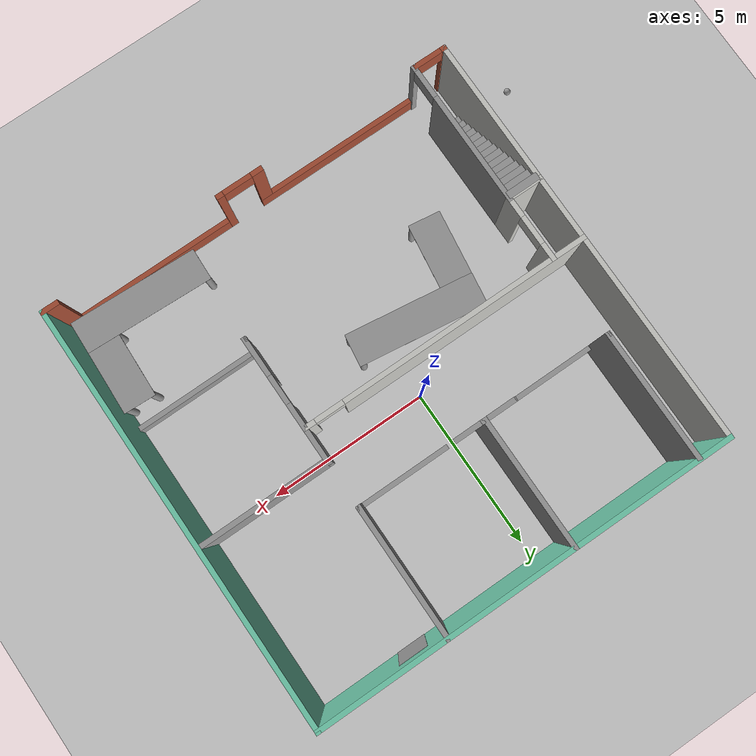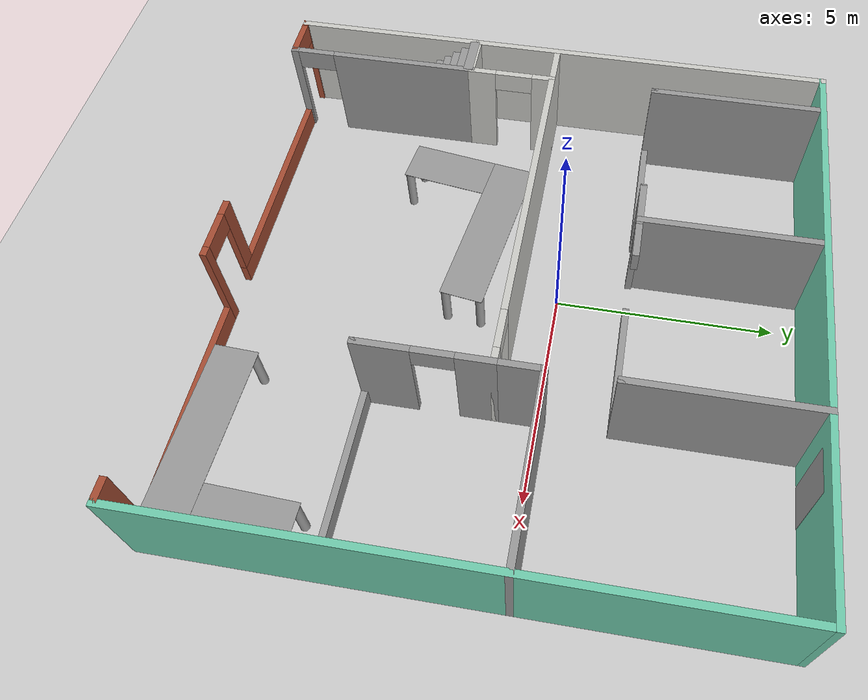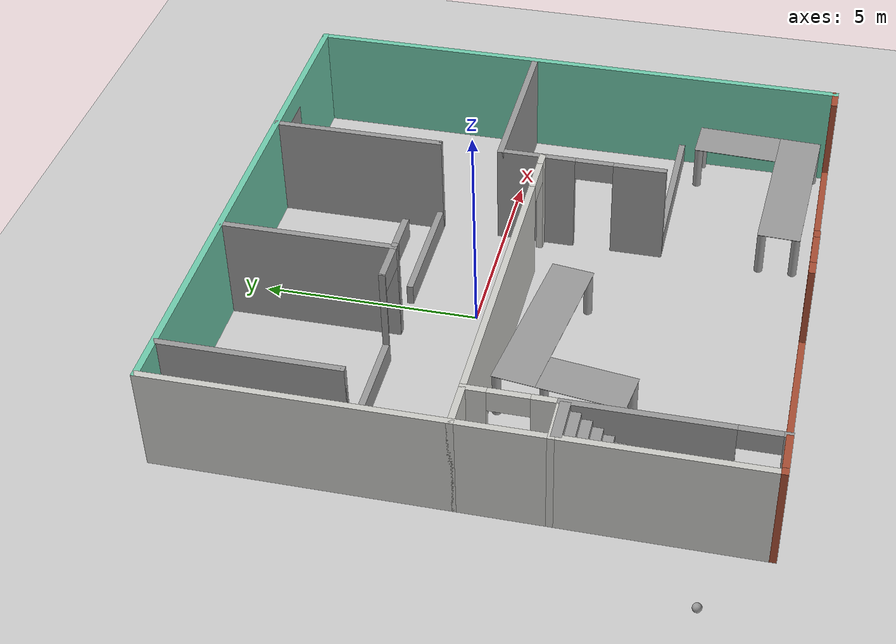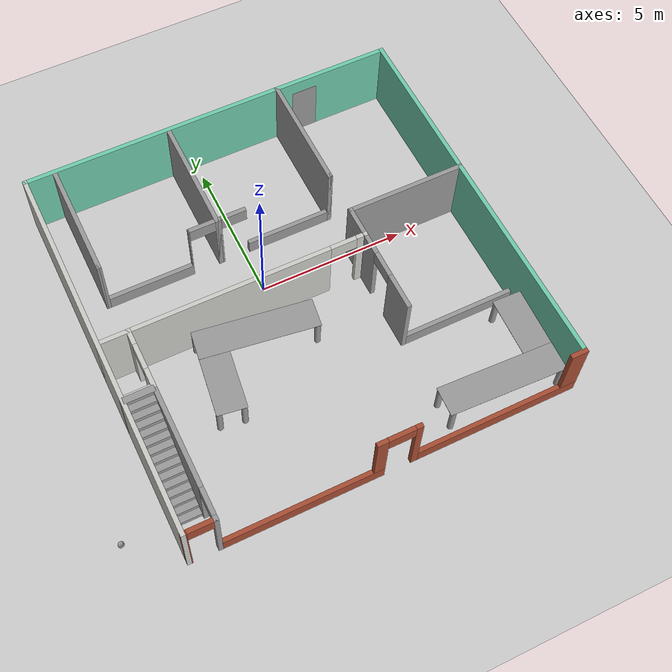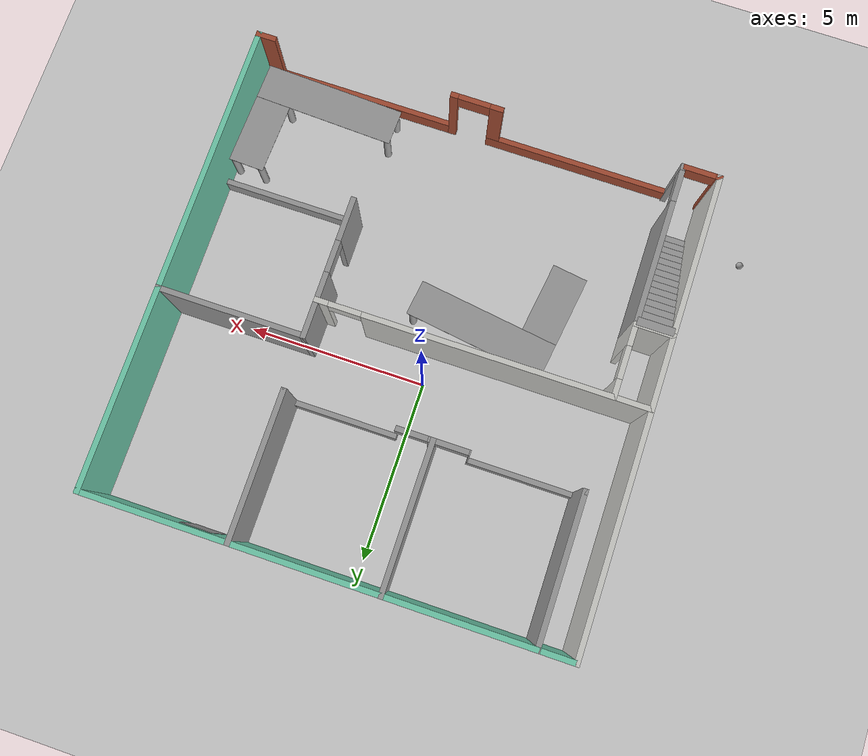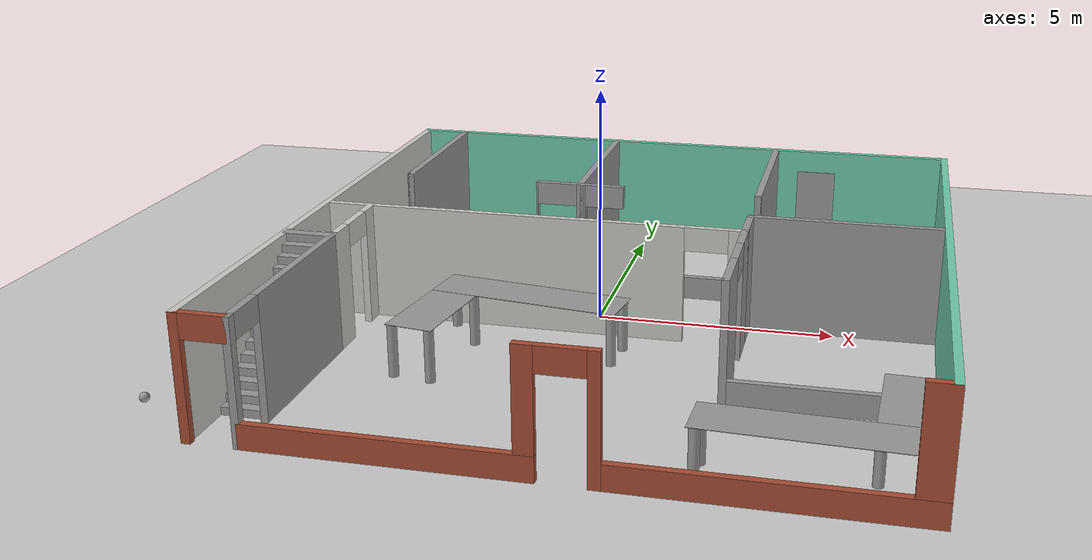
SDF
<sdf version="1.6">
 <world name="default">
  <plugin name="welcome_message" filename="libwelcome_message.so"/>
  <light name="sun" type="directional">
   <pose>0 0 10 0 -0 0</pose>
   <diffuse>0.8 0.8 0.8 1</diffuse>
   <specular>0.2 0.2 0.2 1</specular>
   <attenuation>
    <range>1000</range>
    <constant>0.9</constant>
    <linear>0.01</linear>
    <quadratic>0.001</quadratic>
   </attenuation>
   <direction>-0.5 0.1 -0.9</direction>
  </light>
  <model name="ground_plane">
   <static>1</static>
   <link name="link">
    <collision name="collision">
     <geometry><plane><normal>0 0 1</normal><size>100 100</size></plane></geometry>
     <surface>
      <contact><collide_bitmask>65535</collide_bitmask></contact>
      <friction><ode><mu>100</mu><mu2>50</mu2></ode></friction>
     </surface>
    </collision>
    <visual name="visual">
     <cast_shadows>0</cast_shadows>
     <geometry><plane><normal>0 0 1</normal><size>100 100</size></plane></geometry>
     <material>
      <script><uri>file://media/materials/scripts/gazebo.material</uri><name>Gazebo/Grey</name></script>
     </material>
    </visual>
   </link>
  </model>
  <gravity>0 0 -9.8</gravity>
  <magnetic_field>6e-06 2.3e-05 -4.2e-05</magnetic_field>
  <atmosphere type="adiabatic"/>
  <physics name="default_physics" default="0" type="ode">
   <max_step_size>0.001</max_step_size>
   <real_time_factor>1</real_time_factor>
   <real_time_update_rate>1000</real_time_update_rate>
  </physics>
  <scene><ambient>0.4 0.4 0.4 1</ambient><background>0.7 0.7 0.7 1</background><shadows>1</shadows></scene>
  <spherical_coordinates>
   <surface_model>EARTH_WGS84</surface_model>
   <latitude_deg>0</latitude_deg>
   <longitude_deg>0</longitude_deg>
   <elevation>0</elevation>
   <heading_deg>0</heading_deg>
  </spherical_coordinates>
  <model name="HB_greenLabs">
   <pose>0.67281 -0.88547 0 0 -0 0</pose>
   <link name="Door_8">
    <collision name="Door_8_Collision">
     <geometry><box><size>0.9 0.17 2</size></box></geometry>
     <pose>0 0 1 0 -0 0</pose>
    </collision>
    <visual name="Door_8_Visual">
     <pose>0 0 1 0 -0 0</pose>
     <geometry><box><size>0.9 0.17 2</size></box></geometry>
     <material>
      <script><uri>file://media/materials/scripts/gazebo.material</uri><name>Gazebo/Grey</name></script>
     </material>
    </visual>
    <pose>3.5 6.5 0 0 -0 0</pose>
   </link>
   <link name="Stairs_0">
    <visual name="Stairs_0_Visual_0">
     <pose>-6 -5.26467 0.083333 0 -0 -3.14159</pose>
     <geometry><box><size>1 0.226667 0.166667</size></box></geometry>
     <material>
      <script><uri>file://media/materials/scripts/gazebo.material</uri><name>Gazebo/Grey</name></script>
      <ambient>1 1 1 1</ambient>
     </material>
     <meta><layer>0</layer></meta>
    </visual>
    <collision name="Stairs_0_Collision_0">
     <geometry><box><size>1 0.226667 0.166667</size></box></geometry>
     <pose>-6 -5.26467 0.083333 0 -0 -3.14159</pose>
    </collision>
    <visual name="Stairs_0_Visual_1">
     <pose>-6 -5.038 0.25 0 -0 -3.14159</pose>
     <geometry><box><size>1 0.226667 0.166667</size></box></geometry>
     <material>
      <script><uri>file://media/materials/scripts/gazebo.material</uri><name>Gazebo/Grey</name></script>
      <ambient>1 1 1 1</ambient>
     </material>
     <meta><layer>0</layer></meta>
    </visual>
    <collision name="Stairs_0_Collision_1">
     <geometry><box><size>1 0.226667 0.166667</size></box></geometry>
     <pose>-6 -5.038 0.25 0 -0 -3.14159</pose>
    </collision>
    <visual name="Stairs_0_Visual_2">
     <pose>-6 -4.81133 0.416667 0 -0 -3.14159</pose>
     <geometry><box><size>1 0.226667 0.166667</size></box></geometry>
     <material>
      <script><uri>file://media/materials/scripts/gazebo.material</uri><name>Gazebo/Grey</name></script>
      <ambient>1 1 1 1</ambient>
     </material>
     <meta><layer>0</layer></meta>
    </visual>
    <collision name="Stairs_0_Collision_2">
     <geometry><box><size>1 0.226667 0.166667</size></box></geometry>
     <pose>-6 -4.81133 0.416667 0 -0 -3.14159</pose>
    </collision>
    <visual name="Stairs_0_Visual_3">
     <pose>-6 -4.58467 0.583333 0 -0 -3.14159</pose>
     <geometry><box><size>1 0.226667 0.166667</size></box></geometry>
     <material>
      <script><uri>file://media/materials/scripts/gazebo.material</uri><name>Gazebo/Grey</name></script>
      <ambient>1 1 1 1</ambient>
     </material>
     <meta><layer>0</layer></meta>
    </visual>
    <collision name="Stairs_0_Collision_3">
     <geometry><box><size>1 0.226667 0.166667</size></box></geometry>
     <pose>-6 -4.58467 0.583333 0 -0 -3.14159</pose>
    </collision>
    <visual name="Stairs_0_Visual_4">
     <pose>-6 -4.358 0.75 0 -0 -3.14159</pose>
     <geometry><box><size>1 0.226667 0.166667</size></box></geometry>
     <material>
      <script><uri>file://media/materials/scripts/gazebo.material</uri><name>Gazebo/Grey</name></script>
      <ambient>1 1 1 1</ambient>
     </material>
     <meta><layer>0</layer></meta>
    </visual>
    <collision name="Stairs_0_Collision_4">
     <geometry><box><size>1 0.226667 0.166667</size></box></geometry>
     <pose>-6 -4.358 0.75 0 -0 -3.14159</pose>
    </collision>
    <visual name="Stairs_0_Visual_5">
     <pose>-6 -4.13133 0.916667 0 -0 -3.14159</pose>
     <geometry><box><size>1 0.226667 0.166667</size></box></geometry>
     <material>
      <script><uri>file://media/materials/scripts/gazebo.material</uri><name>Gazebo/Grey</name></script>
      <ambient>1 1 1 1</ambient>
     </material>
     <meta><layer>0</layer></meta>
    </visual>
    <collision name="Stairs_0_Collision_5">
     <geometry><box><size>1 0.226667 0.166667</size></box></geometry>
     <pose>-6 -4.13133 0.916667 0 -0 -3.14159</pose>
    </collision>
    <visual name="Stairs_0_Visual_6">
     <pose>-6 -3.90467 1.08333 0 -0 -3.14159</pose>
     <geometry><box><size>1 0.226667 0.166667</size></box></geometry>
     <material>
      <script><uri>file://media/materials/scripts/gazebo.material</uri><name>Gazebo/Grey</name></script>
      <ambient>1 1 1 1</ambient>
     </material>
     <meta><layer>0</layer></meta>
    </visual>
    <collision name="Stairs_0_Collision_6">
     <geometry><box><size>1 0.226667 0.166667</size></box></geometry>
     <pose>-6 -3.90467 1.08333 0 -0 -3.14159</pose>
    </collision>
    <visual name="Stairs_0_Visual_7">
     <pose>-6 -3.678 1.25 0 -0 -3.14159</pose>
     <geometry><box><size>1 0.226667 0.166667</size></box></geometry>
     <material>
      <script><uri>file://media/materials/scripts/gazebo.material</uri><name>Gazebo/Grey</name></script>
      <ambient>1 1 1 1</ambient>
     </material>
     <meta><layer>0</layer></meta>
    </visual>
    <collision name="Stairs_0_Collision_7">
     <geometry><box><size>1 0.226667 0.166667</size></box></geometry>
     <pose>-6 -3.678 1.25 0 -0 -3.14159</pose>
    </collision>
    <visual name="Stairs_0_Visual_8">
     <pose>-6 -3.45133 1.41667 0 -0 -3.14159</pose>
     <geometry><box><size>1 0.226667 0.166667</size></box></geometry>
     <material>
      <script><uri>file://media/materials/scripts/gazebo.material</uri><name>Gazebo/Grey</name></script>
      <ambient>1 1 1 1</ambient>
     </material>
     <meta><layer>0</layer></meta>
    </visual>
    <collision name="Stairs_0_Collision_8">
     <geometry><box><size>1 0.226667 0.166667</size></box></geometry>
     <pose>-6 -3.45133 1.41667 0 -0 -3.14159</pose>
    </collision>
    <visual name="Stairs_0_Visual_9">
     <pose>-6 -3.22467 1.58333 0 -0 -3.14159</pose>
     <geometry><box><size>1 0.226667 0.166667</size></box></geometry>
     <material>
      <script><uri>file://media/materials/scripts/gazebo.material</uri><name>Gazebo/Grey</name></script>
      <ambient>1 1 1 1</ambient>
     </material>
     <meta><layer>0</layer></meta>
    </visual>
    <collision name="Stairs_0_Collision_9">
     <geometry><box><size>1 0.226667 0.166667</size></box></geometry>
     <pose>-6 -3.22467 1.58333 0 -0 -3.14159</pose>
    </collision>
    <visual name="Stairs_0_Visual_10">
     <pose>-6 -2.998 1.75 0 -0 -3.14159</pose>
     <geometry><box><size>1 0.226667 0.166667</size></box></geometry>
     <material>
      <script><uri>file://media/materials/scripts/gazebo.material</uri><name>Gazebo/Grey</name></script>
      <ambient>1 1 1 1</ambient>
     </material>
     <meta><layer>0</layer></meta>
    </visual>
    <collision name="Stairs_0_Collision_10">
     <geometry><box><size>1 0.226667 0.166667</size></box></geometry>
     <pose>-6 -2.998 1.75 0 -0 -3.14159</pose>
    </collision>
    <visual name="Stairs_0_Visual_11">
     <pose>-6 -2.77133 1.91667 0 -0 -3.14159</pose>
     <geometry><box><size>1 0.226667 0.166667</size></box></geometry>
     <material>
      <script><uri>file://media/materials/scripts/gazebo.material</uri><name>Gazebo/Grey</name></script>
      <ambient>1 1 1 1</ambient>
     </material>
     <meta><layer>0</layer></meta>
    </visual>
    <collision name="Stairs_0_Collision_11">
     <geometry><box><size>1 0.226667 0.166667</size></box></geometry>
     <pose>-6 -2.77133 1.91667 0 -0 -3.14159</pose>
    </collision>
    <visual name="Stairs_0_Visual_12">
     <pose>-6 -2.54467 2.08333 0 -0 -3.14159</pose>
     <geometry><box><size>1 0.226667 0.166667</size></box></geometry>
     <material>
      <script><uri>file://media/materials/scripts/gazebo.material</uri><name>Gazebo/Grey</name></script>
      <ambient>1 1 1 1</ambient>
     </material>
     <meta><layer>0</layer></meta>
    </visual>
    <collision name="Stairs_0_Collision_12">
     <geometry><box><size>1 0.226667 0.166667</size></box></geometry>
     <pose>-6 -2.54467 2.08333 0 -0 -3.14159</pose>
    </collision>
    <visual name="Stairs_0_Visual_13">
     <pose>-6 -2.318 2.25 0 -0 -3.14159</pose>
     <geometry><box><size>1 0.226667 0.166667</size></box></geometry>
     <material>
      <script><uri>file://media/materials/scripts/gazebo.material</uri><name>Gazebo/Grey</name></script>
      <ambient>1 1 1 1</ambient>
     </material>
     <meta><layer>0</layer></meta>
    </visual>
    <collision name="Stairs_0_Collision_13">
     <geometry><box><size>1 0.226667 0.166667</size></box></geometry>
     <pose>-6 -2.318 2.25 0 -0 -3.14159</pose>
    </collision>
    <visual name="Stairs_0_Visual_14">
     <pose>-6 -2.09133 2.41667 0 -0 -3.14159</pose>
     <geometry><box><size>1 0.226667 0.166667</size></box></geometry>
     <material>
      <script><uri>file://media/materials/scripts/gazebo.material</uri><name>Gazebo/Grey</name></script>
      <ambient>1 1 1 1</ambient>
     </material>
     <meta><layer>0</layer></meta>
    </visual>
    <collision name="Stairs_0_Collision_14">
     <geometry><box><size>1 0.226667 0.166667</size></box></geometry>
     <pose>-6 -2.09133 2.41667 0 -0 -3.14159</pose>
    </collision>
   </link>
   <link name="Wall_11">
    <pose>0 -6.5 0 0 -0 0</pose>
    <visual name="Wall_11_Visual_0">
     <pose>-6.48238 0 1.25 0 -0 0</pose>
     <geometry><box><size>0.185236 0.15 2.5</size></box></geometry>
     <material>
      <script><uri>file://media/materials/scripts/gazebo.material</uri><name>Gazebo/Bricks</name></script>
      <ambient>1 1 1 1</ambient>
     </material>
     <meta><layer>0</layer></meta>
    </visual>
    <collision name="Wall_11_Collision_0">
     <geometry><box><size>0.185236 0.15 2.5</size></box></geometry>
     <pose>-6.48238 0 1.25 0 -0 0</pose>
    </collision>
    <visual name="Wall_11_Visual_1">
     <pose>-2.80803 0 0.25 0 -0 0</pose>
     <geometry><box><size>5.36346 0.15 0.5</size></box></geometry>
     <material>
      <script><uri>file://media/materials/scripts/gazebo.material</uri><name>Gazebo/Bricks</name></script>
      <ambient>1 1 1 1</ambient>
     </material>
     <meta><layer>0</layer></meta>
    </visual>
    <collision name="Wall_11_Collision_1">
     <geometry><box><size>5.36346 0.15 0.5</size></box></geometry>
     <pose>-2.80803 0 0.25 0 -0 0</pose>
    </collision>
    <visual name="Wall_11_Visual_2">
     <pose>0.88685 0 1.25 0 -0 0</pose>
     <geometry><box><size>0.226301 0.15 2.5</size></box></geometry>
     <material>
      <script><uri>file://media/materials/scripts/gazebo.material</uri><name>Gazebo/Bricks</name></script>
      <ambient>1 1 1 1</ambient>
     </material>
     <meta><layer>0</layer></meta>
    </visual>
    <collision name="Wall_11_Collision_2">
     <geometry><box><size>0.226301 0.15 2.5</size></box></geometry>
     <pose>0.88685 0 1.25 0 -0 0</pose>
    </collision>
    <visual name="Wall_11_Visual_3">
     <pose>3.7875 0 0.25 0 -0 0</pose>
     <geometry><box><size>5.575 0.15 0.5</size></box></geometry>
     <material>
      <script><uri>file://media/materials/scripts/gazebo.material</uri><name>Gazebo/Bricks</name></script>
      <ambient>1 1 1 1</ambient>
     </material>
     <meta><layer>0</layer></meta>
    </visual>
    <collision name="Wall_11_Collision_3">
     <geometry><box><size>5.575 0.15 0.5</size></box></geometry>
     <pose>3.7875 0 0.25 0 -0 0</pose>
    </collision>
    <visual name="Wall_11_Visual_4">
     <pose>-0.31315 0 1.5 0 -0 0</pose>
     <geometry><box><size>0.373699 0.15 2</size></box></geometry>
     <material>
      <script><uri>file://media/materials/scripts/gazebo.material</uri><name>Gazebo/Bricks</name></script>
      <ambient>1 1 1 1</ambient>
     </material>
     <meta><layer>0</layer></meta>
    </visual>
    <collision name="Wall_11_Collision_4">
     <geometry><box><size>0.373699 0.15 2</size></box></geometry>
     <pose>-0.31315 0 1.5 0 -0 0</pose>
    </collision>
    <visual name="Wall_11_Visual_5">
     <pose>-0.31315 0 1.5 0 -0 0</pose>
     <geometry><box><size>0.373699 0.15 2</size></box></geometry>
     <material>
      <script><uri>file://media/materials/scripts/gazebo.material</uri><name>Gazebo/Bricks</name></script>
      <ambient>1 1 1 1</ambient>
     </material>
     <meta><layer>0</layer></meta>
    </visual>
    <collision name="Wall_11_Collision_5">
     <geometry><box><size>0.373699 0.15 2</size></box></geometry>
     <pose>-0.31315 0 1.5 0 -0 0</pose>
    </collision>
    <visual name="Wall_11_Visual_6">
     <pose>6.2875 0 1.5 0 -0 0</pose>
     <geometry><box><size>0.575 0.15 2</size></box></geometry>
     <material>
      <script><uri>file://media/materials/scripts/gazebo.material</uri><name>Gazebo/Bricks</name></script>
      <ambient>1 1 1 1</ambient>
     </material>
     <meta><layer>0</layer></meta>
    </visual>
    <collision name="Wall_11_Collision_6">
     <geometry><box><size>0.575 0.15 2</size></box></geometry>
     <pose>6.2875 0 1.5 0 -0 0</pose>
    </collision>
    <visual name="Wall_11_Visual_7">
     <pose>-5.94488 0 2.25 0 -0 0</pose>
     <geometry><box><size>0.889764 0.15 0.5</size></box></geometry>
     <material>
      <script><uri>file://media/materials/scripts/gazebo.material</uri><name>Gazebo/Bricks</name></script>
      <ambient>1 1 1 1</ambient>
     </material>
     <meta><layer>0</layer></meta>
    </visual>
    <collision name="Wall_11_Collision_7">
     <geometry><box><size>0.889764 0.15 0.5</size></box></geometry>
     <pose>-5.94488 0 2.25 0 -0 0</pose>
    </collision>
    <visual name="Wall_11_Visual_8">
     <pose>0.323699 0 2.25 0 -0 0</pose>
     <geometry><box><size>0.9 0.15 0.5</size></box></geometry>
     <material>
      <script><uri>file://media/materials/scripts/gazebo.material</uri><name>Gazebo/Bricks</name></script>
      <ambient>1 1 1 1</ambient>
     </material>
     <meta><layer>0</layer></meta>
    </visual>
    <collision name="Wall_11_Collision_8">
     <geometry><box><size>0.9 0.15 0.5</size></box></geometry>
     <pose>0.323699 0 2.25 0 -0 0</pose>
    </collision>
    <visual name="Wall_11_Visual_9">
     <pose>0.323699 0 2.25 0 -0 0</pose>
     <geometry><box><size>0.9 0.15 0.5</size></box></geometry>
     <material>
      <script><uri>file://media/materials/scripts/gazebo.material</uri><name>Gazebo/Bricks</name></script>
      <ambient>1 1 1 1</ambient>
     </material>
     <meta><layer>0</layer></meta>
    </visual>
    <collision name="Wall_11_Collision_9">
     <geometry><box><size>0.9 0.15 0.5</size></box></geometry>
     <pose>0.323699 0 2.25 0 -0 0</pose>
    </collision>
   </link>
   <link name="Wall_12">
    <collision name="Wall_12_Collision">
     <geometry><box><size>13.15 0.15 2.5</size></box></geometry>
     <pose>0 0 1.25 0 -0 0</pose>
    </collision>
    <visual name="Wall_12_Visual">
     <pose>0 0 1.25 0 -0 0</pose>
     <geometry><box><size>13.15 0.15 2.5</size></box></geometry>
     <material>
      <script><uri>file://media/materials/scripts/gazebo.material</uri><name>Gazebo/Grey</name></script>
      <ambient>0.435294 0.796078 0.67451 1</ambient>
     </material>
     <meta><layer>0</layer></meta>
    </visual>
    <pose>6.5 0 0 0 -0 1.5708</pose>
   </link>
   <link name="Wall_14">
    <collision name="Wall_14_Collision">
     <geometry><box><size>13.15 0.15 2.5</size></box></geometry>
     <pose>0 0 1.25 0 -0 0</pose>
    </collision>
    <visual name="Wall_14_Visual">
     <pose>0 0 1.25 0 -0 0</pose>
     <geometry><box><size>13.15 0.15 2.5</size></box></geometry>
     <material>
      <script><uri>file://media/materials/scripts/gazebo.material</uri><name>Gazebo/CeilingTiled</name></script>
      <ambient>0.435294 0.796078 0.67451 1</ambient>
     </material>
     <meta><layer>0</layer></meta>
    </visual>
    <pose>-6.5 0 0 0 -0 1.5708</pose>
   </link>
   <link name="Wall_16">
    <collision name="Wall_16_Collision">
     <geometry><box><size>13.15 0.15 2.5</size></box></geometry>
     <pose>0 0 1.25 0 -0 0</pose>
    </collision>
    <visual name="Wall_16_Visual">
     <pose>0 0 1.25 0 -0 0</pose>
     <geometry><box><size>13.15 0.15 2.5</size></box></geometry>
     <material>
      <script><uri>file://media/materials/scripts/gazebo.material</uri><name>Gazebo/Grey</name></script>
      <ambient>0.435294 0.796078 0.67451 1</ambient>
     </material>
     <meta><layer>0</layer></meta>
    </visual>
    <pose>0 6.5 0 0 -0 0</pose>
   </link>
   <link name="Wall_18">
    <pose>-5.5 -4.25 0 0 -0 1.5708</pose>
    <visual name="Wall_18_Visual_0">
     <pose>-2.23145 0 1.25 0 -0 0</pose>
     <geometry><box><size>0.187101 0.15 2.5</size></box></geometry>
     <material>
      <script><uri>file://media/materials/scripts/gazebo.material</uri><name>Gazebo/Grey</name></script>
      <ambient>1 1 1 1</ambient>
     </material>
     <meta><layer>0</layer></meta>
    </visual>
    <collision name="Wall_18_Collision_0">
     <geometry><box><size>0.187101 0.15 2.5</size></box></geometry>
     <pose>-2.23145 0 1.25 0 -0 0</pose>
    </collision>
    <visual name="Wall_18_Visual_1">
     <pose>0.54355 0 1.25 0 -0 0</pose>
     <geometry><box><size>3.5629 0.15 2.5</size></box></geometry>
     <material>
      <script><uri>file://media/materials/scripts/gazebo.material</uri><name>Gazebo/Grey</name></script>
      <ambient>1 1 1 1</ambient>
     </material>
     <meta><layer>0</layer></meta>
    </visual>
    <collision name="Wall_18_Collision_1">
     <geometry><box><size>3.5629 0.15 2.5</size></box></geometry>
     <pose>0.54355 0 1.25 0 -0 0</pose>
    </collision>
    <visual name="Wall_18_Visual_2">
     <pose>-1.6879 0 2.25 0 -0 0</pose>
     <geometry><box><size>0.9 0.15 0.5</size></box></geometry>
     <material>
      <script><uri>file://media/materials/scripts/gazebo.material</uri><name>Gazebo/Grey</name></script>
      <ambient>1 1 1 1</ambient>
     </material>
     <meta><layer>0</layer></meta>
    </visual>
    <collision name="Wall_18_Collision_2">
     <geometry><box><size>0.9 0.15 0.5</size></box></geometry>
     <pose>-1.6879 0 2.25 0 -0 0</pose>
    </collision>
   </link>
   <link name="Wall_20">
    <collision name="Wall_20_Collision">
     <geometry><box><size>1.15 0.15 2.5</size></box></geometry>
     <pose>0 0 1.25 0 -0 0</pose>
    </collision>
    <visual name="Wall_20_Visual">
     <pose>0 0 1.25 0 -0 0</pose>
     <geometry><box><size>1.15 0.15 2.5</size></box></geometry>
     <material>
      <script><uri>file://media/materials/scripts/gazebo.material</uri><name>Gazebo/CeilingTiled</name></script>
      <ambient>1 1 1 1</ambient>
     </material>
     <meta><layer>0</layer></meta>
    </visual>
    <pose>-6 -2 0 0 -0 0</pose>
   </link>
   <link name="Wall_22">
    <pose>-2 0 0 0 -0 0</pose>
    <visual name="Wall_22_Visual_0">
     <pose>-0.647075 0 1.25 0 -0 0</pose>
     <geometry><box><size>7.85585 0.15 2.5</size></box></geometry>
     <material>
      <script><uri>file://media/materials/scripts/gazebo.material</uri><name>Gazebo/CeilingTiled</name></script>
      <ambient>1 1 1 1</ambient>
     </material>
     <meta><layer>0</layer></meta>
    </visual>
    <collision name="Wall_22_Collision_0">
     <geometry><box><size>7.85585 0.15 2.5</size></box></geometry>
     <pose>-0.647075 0 1.25 0 -0 0</pose>
    </collision>
    <visual name="Wall_22_Visual_1">
     <pose>4.37793 0 1.25 0 -0 0</pose>
     <geometry><box><size>0.39415 0.15 2.5</size></box></geometry>
     <material>
      <script><uri>file://media/materials/scripts/gazebo.material</uri><name>Gazebo/CeilingTiled</name></script>
      <ambient>1 1 1 1</ambient>
     </material>
     <meta><layer>0</layer></meta>
    </visual>
    <collision name="Wall_22_Collision_1">
     <geometry><box><size>0.39415 0.15 2.5</size></box></geometry>
     <pose>4.37793 0 1.25 0 -0 0</pose>
    </collision>
    <visual name="Wall_22_Visual_2">
     <pose>3.73085 0 2.25 0 -0 0</pose>
     <geometry><box><size>0.9 0.15 0.5</size></box></geometry>
     <material>
      <script><uri>file://media/materials/scripts/gazebo.material</uri><name>Gazebo/CeilingTiled</name></script>
      <ambient>1 1 1 1</ambient>
     </material>
     <meta><layer>0</layer></meta>
    </visual>
    <collision name="Wall_22_Collision_2">
     <geometry><box><size>0.9 0.15 0.5</size></box></geometry>
     <pose>3.73085 0 2.25 0 -0 0</pose>
    </collision>
   </link>
   <link name="Wall_26">
    <pose>-5.5 -1 0 0 -0 1.5708</pose>
    <visual name="Wall_26_Visual_0">
     <pose>-0.734323 0 1.25 0 -0 0</pose>
     <geometry><box><size>0.681355 0.15 2.5</size></box></geometry>
     <material>
      <script><uri>file://media/materials/scripts/gazebo.material</uri><name>Gazebo/CeilingTiled</name></script>
      <ambient>1 1 1 1</ambient>
     </material>
     <meta><layer>0</layer></meta>
    </visual>
    <collision name="Wall_26_Collision_0">
     <geometry><box><size>0.681355 0.15 2.5</size></box></geometry>
     <pose>-0.734323 0 1.25 0 -0 0</pose>
    </collision>
    <visual name="Wall_26_Visual_1">
     <pose>0.790677 0 1.25 0 -0 0</pose>
     <geometry><box><size>0.568645 0.15 2.5</size></box></geometry>
     <material>
      <script><uri>file://media/materials/scripts/gazebo.material</uri><name>Gazebo/CeilingTiled</name></script>
      <ambient>1 1 1 1</ambient>
     </material>
     <meta><layer>0</layer></meta>
    </visual>
    <collision name="Wall_26_Collision_1">
     <geometry><box><size>0.568645 0.15 2.5</size></box></geometry>
     <pose>0.790677 0 1.25 0 -0 0</pose>
    </collision>
    <visual name="Wall_26_Visual_2">
     <pose>0.056355 0 2.25 0 -0 0</pose>
     <geometry><box><size>0.9 0.15 0.5</size></box></geometry>
     <material>
      <script><uri>file://media/materials/scripts/gazebo.material</uri><name>Gazebo/CeilingTiled</name></script>
      <ambient>1 1 1 1</ambient>
     </material>
     <meta><layer>0</layer></meta>
    </visual>
    <collision name="Wall_26_Collision_2">
     <geometry><box><size>0.9 0.15 0.5</size></box></geometry>
     <pose>0.056355 0 2.25 0 -0 0</pose>
    </collision>
   </link>
   <link name="Wall_28">
    <pose>2.5 -1.425 0 0 0 -1.5708</pose>
    <visual name="Wall_28_Visual_0">
     <pose>-1.07292 0 1.25 0 -0 0</pose>
     <geometry><box><size>0.854154 0.15 2.5</size></box></geometry>
     <material>
      <script><uri>file://media/materials/scripts/gazebo.material</uri><name>Gazebo/Grey</name></script>
      <ambient>1 1 1 1</ambient>
     </material>
     <meta><layer>0</layer></meta>
    </visual>
    <collision name="Wall_28_Collision_0">
     <geometry><box><size>0.854154 0.15 2.5</size></box></geometry>
     <pose>-1.07292 0 1.25 0 -0 0</pose>
    </collision>
    <visual name="Wall_28_Visual_1">
     <pose>0.877077 0 1.25 0 -0 0</pose>
     <geometry><box><size>1.24585 0.15 2.5</size></box></geometry>
     <material>
      <script><uri>file://media/materials/scripts/gazebo.material</uri><name>Gazebo/Grey</name></script>
      <ambient>1 1 1 1</ambient>
     </material>
     <meta><layer>0</layer></meta>
    </visual>
    <collision name="Wall_28_Collision_1">
     <geometry><box><size>1.24585 0.15 2.5</size></box></geometry>
     <pose>0.877077 0 1.25 0 -0 0</pose>
    </collision>
    <visual name="Wall_28_Visual_2">
     <pose>-0.195846 0 2.25 0 -0 0</pose>
     <geometry><box><size>0.9 0.15 0.5</size></box></geometry>
     <material>
      <script><uri>file://media/materials/scripts/gazebo.material</uri><name>Gazebo/Grey</name></script>
      <ambient>1 1 1 1</ambient>
     </material>
     <meta><layer>0</layer></meta>
    </visual>
    <collision name="Wall_28_Collision_2">
     <geometry><box><size>0.9 0.15 0.5</size></box></geometry>
     <pose>-0.195846 0 2.25 0 -0 0</pose>
    </collision>
   </link>
   <link name="Wall_30">
    <pose>4.425 -2.85 0 0 -0 0</pose>
    <visual name="Wall_30_Visual_0">
     <pose>-1.9625 0 1.25 0 -0 0</pose>
     <geometry><box><size>0.075 0.15 2.5</size></box></geometry>
     <material>
      <script><uri>file://media/materials/scripts/gazebo.material</uri><name>Gazebo/Grey</name></script>
      <ambient>1 1 1 1</ambient>
     </material>
     <meta><layer>0</layer></meta>
    </visual>
    <collision name="Wall_30_Collision_0">
     <geometry><box><size>0.075 0.15 2.5</size></box></geometry>
     <pose>-1.9625 0 1.25 0 -0 0</pose>
    </collision>
    <visual name="Wall_30_Visual_1">
     <pose>0.0375 0 0.25 0 -0 0</pose>
     <geometry><box><size>3.925 0.15 0.5</size></box></geometry>
     <material>
      <script><uri>file://media/materials/scripts/gazebo.material</uri><name>Gazebo/Grey</name></script>
      <ambient>1 1 1 1</ambient>
     </material>
     <meta><layer>0</layer></meta>
    </visual>
    <collision name="Wall_30_Collision_1">
     <geometry><box><size>3.925 0.15 0.5</size></box></geometry>
     <pose>0.0375 0 0.25 0 -0 0</pose>
    </collision>
   </link>
   <link name="Wall_32">
    <collision name="Wall_32_Collision">
     <geometry><box><size>1.15 0.15 2.5</size></box></geometry>
     <pose>0 0 1.25 0 -0 0</pose>
    </collision>
    <visual name="Wall_32_Visual">
     <pose>0 0 1.25 0 -0 0</pose>
     <geometry><box><size>1.15 0.15 2.5</size></box></geometry>
     <material>
      <script><uri>file://media/materials/scripts/gazebo.material</uri><name>Gazebo/Grey</name></script>
      <ambient>1 1 1 1</ambient>
     </material>
     <meta><layer>0</layer></meta>
    </visual>
    <pose>2.5 0.5 0 0 -0 1.5708</pose>
   </link>
   <link name="Wall_33">
    <collision name="Wall_33_Collision">
     <geometry><box><size>4.15 0.15 2.5</size></box></geometry>
     <pose>0 0 1.25 0 -0 0</pose>
    </collision>
    <visual name="Wall_33_Visual">
     <pose>0 0 1.25 0 -0 0</pose>
     <geometry><box><size>4.15 0.15 2.5</size></box></geometry>
     <material>
      <script><uri>file://media/materials/scripts/gazebo.material</uri><name>Gazebo/Grey</name></script>
      <ambient>1 1 1 1</ambient>
     </material>
     <meta><layer>0</layer></meta>
    </visual>
    <pose>4.5 1 0 0 -0 0</pose>
   </link>
   <link name="Wall_35">
    <collision name="Wall_35_Collision">
     <geometry><box><size>4.15 0.15 2.5</size></box></geometry>
     <pose>0 0 1.25 0 -0 0</pose>
    </collision>
    <visual name="Wall_35_Visual">
     <pose>0 0 1.25 0 -0 0</pose>
     <geometry><box><size>4.15 0.15 2.5</size></box></geometry>
     <material>
      <script><uri>file://media/materials/scripts/gazebo.material</uri><name>Gazebo/Grey</name></script>
      <ambient>1 1 1 1</ambient>
     </material>
     <meta><layer>0</layer></meta>
    </visual>
    <pose>-5.5 4.5 0 0 0 -1.5708</pose>
   </link>
   <link name="Wall_37">
    <pose>-1.5 2.5 0 0 -0 0</pose>
    <visual name="Wall_37_Visual_0">
     <pose>-4.0375 0 1.25 0 -0 0</pose>
     <geometry><box><size>0.075 0.15 2.5</size></box></geometry>
     <material>
      <script><uri>file://media/materials/scripts/gazebo.material</uri><name>Gazebo/Grey</name></script>
      <ambient>1 1 1 1</ambient>
     </material>
     <meta><layer>0</layer></meta>
    </visual>
    <collision name="Wall_37_Collision_0">
     <geometry><box><size>0.075 0.15 2.5</size></box></geometry>
     <pose>-4.0375 0 1.25 0 -0 0</pose>
    </collision>
    <visual name="Wall_37_Visual_1">
     <pose>0.033157 0 1.25 0 -0 0</pose>
     <geometry><box><size>0.196044 0.15 2.5</size></box></geometry>
     <material>
      <script><uri>file://media/materials/scripts/gazebo.material</uri><name>Gazebo/Grey</name></script>
      <ambient>1 1 1 1</ambient>
     </material>
     <meta><layer>0</layer></meta>
    </visual>
    <collision name="Wall_37_Collision_1">
     <geometry><box><size>0.196044 0.15 2.5</size></box></geometry>
     <pose>0.033157 0 1.25 0 -0 0</pose>
    </collision>
    <visual name="Wall_37_Visual_2">
     <pose>2.55309 0 0.25 0 -0 0</pose>
     <geometry><box><size>3.04382 0.15 0.5</size></box></geometry>
     <material>
      <script><uri>file://media/materials/scripts/gazebo.material</uri><name>Gazebo/Grey</name></script>
      <ambient>1 1 1 1</ambient>
     </material>
     <meta><layer>0</layer></meta>
    </visual>
    <collision name="Wall_37_Collision_2">
     <geometry><box><size>3.04382 0.15 0.5</size></box></geometry>
     <pose>2.55309 0 0.25 0 -0 0</pose>
    </collision>
    <visual name="Wall_37_Visual_3">
     <pose>-2.48243 0 0.25 0 -0 0</pose>
     <geometry><box><size>3.03514 0.15 0.5</size></box></geometry>
     <material>
      <script><uri>file://media/materials/scripts/gazebo.material</uri><name>Gazebo/Grey</name></script>
      <ambient>1 1 1 1</ambient>
     </material>
     <meta><layer>0</layer></meta>
    </visual>
    <collision name="Wall_37_Collision_3">
     <geometry><box><size>3.03514 0.15 0.5</size></box></geometry>
     <pose>-2.48243 0 0.25 0 -0 0</pose>
    </collision>
    <visual name="Wall_37_Visual_4">
     <pose>4.0375 0 1.5 0 -0 0</pose>
     <geometry><box><size>0.075 0.15 2</size></box></geometry>
     <material>
      <script><uri>file://media/materials/scripts/gazebo.material</uri><name>Gazebo/Grey</name></script>
      <ambient>1 1 1 1</ambient>
     </material>
     <meta><layer>0</layer></meta>
    </visual>
    <collision name="Wall_37_Collision_4">
     <geometry><box><size>0.075 0.15 2</size></box></geometry>
     <pose>4.0375 0 1.5 0 -0 0</pose>
    </collision>
    <visual name="Wall_37_Visual_5">
     <pose>-0.982432 0 1.5 0 -0 0</pose>
     <geometry><box><size>0.035136 0.15 2</size></box></geometry>
     <material>
      <script><uri>file://media/materials/scripts/gazebo.material</uri><name>Gazebo/Grey</name></script>
      <ambient>1 1 1 1</ambient>
     </material>
     <meta><layer>0</layer></meta>
    </visual>
    <collision name="Wall_37_Collision_5">
     <geometry><box><size>0.035136 0.15 2</size></box></geometry>
     <pose>-0.982432 0 1.5 0 -0 0</pose>
    </collision>
    <visual name="Wall_37_Visual_6">
     <pose>-0.982432 0 1.5 0 -0 0</pose>
     <geometry><box><size>0.035136 0.15 2</size></box></geometry>
     <material>
      <script><uri>file://media/materials/scripts/gazebo.material</uri><name>Gazebo/Grey</name></script>
      <ambient>1 1 1 1</ambient>
     </material>
     <meta><layer>0</layer></meta>
    </visual>
    <collision name="Wall_37_Collision_6">
     <geometry><box><size>0.035136 0.15 2</size></box></geometry>
     <pose>-0.982432 0 1.5 0 -0 0</pose>
    </collision>
    <visual name="Wall_37_Visual_7">
     <pose>0.56559 0 2.25 0 -0 0</pose>
     <geometry><box><size>0.868821 0.15 0.5</size></box></geometry>
     <material>
      <script><uri>file://media/materials/scripts/gazebo.material</uri><name>Gazebo/Grey</name></script>
      <ambient>1 1 1 1</ambient>
     </material>
     <meta><layer>0</layer></meta>
    </visual>
    <collision name="Wall_37_Collision_7">
     <geometry><box><size>0.868821 0.15 0.5</size></box></geometry>
     <pose>0.56559 0 2.25 0 -0 0</pose>
    </collision>
    <visual name="Wall_37_Visual_8">
     <pose>-0.514864 0 2.25 0 -0 0</pose>
     <geometry><box><size>0.9 0.15 0.5</size></box></geometry>
     <material>
      <script><uri>file://media/materials/scripts/gazebo.material</uri><name>Gazebo/Grey</name></script>
      <ambient>1 1 1 1</ambient>
     </material>
     <meta><layer>0</layer></meta>
    </visual>
    <collision name="Wall_37_Collision_8">
     <geometry><box><size>0.9 0.15 0.5</size></box></geometry>
     <pose>-0.514864 0 2.25 0 -0 0</pose>
    </collision>
    <visual name="Wall_37_Visual_9">
     <pose>-0.514864 0 2.25 0 -0 0</pose>
     <geometry><box><size>0.9 0.15 0.5</size></box></geometry>
     <material>
      <script><uri>file://media/materials/scripts/gazebo.material</uri><name>Gazebo/Grey</name></script>
      <ambient>1 1 1 1</ambient>
     </material>
     <meta><layer>0</layer></meta>
    </visual>
    <collision name="Wall_37_Collision_9">
     <geometry><box><size>0.9 0.15 0.5</size></box></geometry>
     <pose>-0.514864 0 2.25 0 -0 0</pose>
    </collision>
   </link>
   <link name="Wall_39">
    <collision name="Wall_39_Collision">
     <geometry><box><size>4.15 0.15 2.5</size></box></geometry>
     <pose>0 0 1.25 0 -0 0</pose>
    </collision>
    <visual name="Wall_39_Visual">
     <pose>0 0 1.25 0 -0 0</pose>
     <geometry><box><size>4.15 0.15 2.5</size></box></geometry>
     <material>
      <script><uri>file://media/materials/scripts/gazebo.material</uri><name>Gazebo/Grey</name></script>
      <ambient>1 1 1 1</ambient>
     </material>
     <meta><layer>0</layer></meta>
    </visual>
    <pose>-1.5 4.5 0 0 -0 1.5708</pose>
   </link>
   <link name="Wall_41">
    <collision name="Wall_41_Collision">
     <geometry><box><size>4.15 0.15 2.5</size></box></geometry>
     <pose>0 0 1.25 0 -0 0</pose>
    </collision>
    <visual name="Wall_41_Visual">
     <pose>0 0 1.25 0 -0 0</pose>
     <geometry><box><size>4.15 0.15 2.5</size></box></geometry>
     <material>
      <script><uri>file://media/materials/scripts/gazebo.material</uri><name>Gazebo/Grey</name></script>
      <ambient>1 1 1 1</ambient>
     </material>
     <meta><layer>0</layer></meta>
    </visual>
    <pose>2.5 4.5 0 0 -0 1.5708</pose>
   </link>
   <static>1</static>
  </model>
  <model name="mytable">
   <link name="link_0">
    <pose>-0.78753 0.46744 0.418 0 -0 0</pose>
    <inertial>
     <mass>1</mass>
     <inertia>
      <ixx>0.166667</ixx>
      <ixy>0</ixy>
      <ixz>0</ixz>
      <iyy>0.166667</iyy>
      <iyz>0</iyz>
      <izz>0.166667</izz>
     </inertia>
    </inertial>
    <visual name="visual">
     <geometry><box><size>1 4 0.01</size></box></geometry>
     <material>
      <lighting>1</lighting>
      <script><uri>file://media/materials/scripts/gazebo.material</uri><name>Gazebo/Grey</name></script>
      <shader type="pixel"><normal_map>__default__</normal_map></shader>
      <ambient>0.3 0.3 0.3 1</ambient>
      <diffuse>0.7 0.7 0.7 1</diffuse>
      <specular>0.01 0.01 0.01 1</specular>
      <emissive>0 0 0 1</emissive>
     </material>
    </visual>
    <collision name="collision">
     <geometry><box><size>1 4 0.01</size></box></geometry>
     <surface>
      <friction>
       <ode><mu>1</mu><mu2>1</mu2><fdir1>0 0 0</fdir1><slip1>0</slip1><slip2>0</slip2></ode>
       <torsional>
        <coefficient>1</coefficient>
        <patch_radius>0</patch_radius>
        <surface_radius>0</surface_radius>
        <use_patch_radius>1</use_patch_radius>
        <ode><slip>0</slip></ode>
       </torsional>
      </friction>
      <bounce><restitution_coefficient>0</restitution_coefficient><threshold>1e+06</threshold></bounce>
      <contact>
       <collide_without_contact>0</collide_without_contact>
       <collide_without_contact_bitmask>1</collide_without_contact_bitmask>
       <collide_bitmask>1</collide_bitmask>
       <ode>
        <soft_cfm>0</soft_cfm>
        <soft_erp>0.2</soft_erp>
        <kp>1e+13</kp>
        <kd>1</kd>
        <max_vel>0.01</max_vel>
        <min_depth>0</min_depth>
       </ode>
       <bullet>
        <split_impulse>1</split_impulse>
        <split_impulse_penetration_threshold>-0.01</split_impulse_penetration_threshold>
        <soft_cfm>0</soft_cfm>
        <soft_erp>0.2</soft_erp>
        <kp>1e+13</kp>
        <kd>1</kd>
       </bullet>
      </contact>
     </surface>
    </collision>
   </link>
   <link name="link_0_clone">
    <pose>0.712518 -1.03246 0.416 0 -0 1.5707</pose>
    <inertial>
     <mass>1</mass>
     <inertia>
      <ixx>0.166667</ixx>
      <ixy>0</ixy>
      <ixz>0</ixz>
      <iyy>0.166667</iyy>
      <iyz>0</iyz>
      <izz>0.166667</izz>
     </inertia>
    </inertial>
    <visual name="visual">
     <geometry><box><size>1 2 0.01</size></box></geometry>
     <material>
      <lighting>1</lighting>
      <script><uri>file://media/materials/scripts/gazebo.material</uri><name>Gazebo/Grey</name></script>
      <shader type="pixel"><normal_map>__default__</normal_map></shader>
      <ambient>0.3 0.3 0.3 1</ambient>
      <diffuse>0.7 0.7 0.7 1</diffuse>
      <specular>0.01 0.01 0.01 1</specular>
      <emissive>0 0 0 1</emissive>
     </material>
    </visual>
    <collision name="collision">
     <geometry><box><size>1 2 0.01</size></box></geometry>
     <surface>
      <friction>
       <ode><mu>1</mu><mu2>1</mu2><fdir1>0 0 0</fdir1><slip1>0</slip1><slip2>0</slip2></ode>
       <torsional>
        <coefficient>1</coefficient>
        <patch_radius>0</patch_radius>
        <surface_radius>0</surface_radius>
        <use_patch_radius>1</use_patch_radius>
        <ode><slip>0</slip></ode>
       </torsional>
      </friction>
      <bounce><restitution_coefficient>0</restitution_coefficient><threshold>1e+06</threshold></bounce>
      <contact>
       <collide_without_contact>0</collide_without_contact>
       <collide_without_contact_bitmask>1</collide_without_contact_bitmask>
       <collide_bitmask>1</collide_bitmask>
       <ode>
        <soft_cfm>0</soft_cfm>
        <soft_erp>0.2</soft_erp>
        <kp>1e+13</kp>
        <kd>1</kd>
        <max_vel>0.01</max_vel>
        <min_depth>0</min_depth>
       </ode>
       <bullet>
        <split_impulse>1</split_impulse>
        <split_impulse_penetration_threshold>-0.01</split_impulse_penetration_threshold>
        <soft_cfm>0</soft_cfm>
        <soft_erp>0.2</soft_erp>
        <kp>1e+13</kp>
        <kd>1</kd>
       </bullet>
      </contact>
     </surface>
    </collision>
   </link>
   <link name="link_1">
    <pose>-1.18753 2.32744 -0.139 0 -0 0</pose>
    <inertial>
     <mass>1</mass>
     <inertia><ixx>0.145833</ixx><ixy>0</ixy><ixz>0</ixz><iyy>0.145833</iyy><iyz>0</iyz><izz>0.125</izz></inertia>
    </inertial>
    <visual name="visual">
     <geometry><cylinder><radius>0.1</radius><length>1.1</length></cylinder></geometry>
     <material>
      <lighting>1</lighting>
      <script><uri>file://media/materials/scripts/gazebo.material</uri><name>Gazebo/Grey</name></script>
      <shader type="pixel"><normal_map>__default__</normal_map></shader>
      <ambient>0.3 0.3 0.3 1</ambient>
      <diffuse>0.7 0.7 0.7 1</diffuse>
      <specular>0.01 0.01 0.01 1</specular>
      <emissive>0 0 0 1</emissive>
     </material>
    </visual>
    <collision name="collision">
     <geometry><cylinder><radius>0.1</radius><length>1.1</length></cylinder></geometry>
     <surface>
      <friction>
       <ode><mu>1</mu><mu2>1</mu2><fdir1>0 0 0</fdir1><slip1>0</slip1><slip2>0</slip2></ode>
       <torsional>
        <coefficient>1</coefficient>
        <patch_radius>0</patch_radius>
        <surface_radius>0</surface_radius>
        <use_patch_radius>1</use_patch_radius>
        <ode><slip>0</slip></ode>
       </torsional>
      </friction>
      <bounce><restitution_coefficient>0</restitution_coefficient><threshold>1e+06</threshold></bounce>
      <contact>
       <collide_without_contact>0</collide_without_contact>
       <collide_without_contact_bitmask>1</collide_without_contact_bitmask>
       <collide_bitmask>1</collide_bitmask>
       <ode>
        <soft_cfm>0</soft_cfm>
        <soft_erp>0.2</soft_erp>
        <kp>1e+13</kp>
        <kd>1</kd>
        <max_vel>0.01</max_vel>
        <min_depth>0</min_depth>
       </ode>
       <bullet>
        <split_impulse>1</split_impulse>
        <split_impulse_penetration_threshold>-0.01</split_impulse_penetration_threshold>
        <soft_cfm>0</soft_cfm>
        <soft_erp>0.2</soft_erp>
        <kp>1e+13</kp>
        <kd>1</kd>
       </bullet>
      </contact>
     </surface>
    </collision>
   </link>
   <link name="link_1_clone">
    <pose>-1.18753 -1.43256 -0.139 0 -0 0</pose>
    <inertial>
     <mass>1</mass>
     <inertia><ixx>0.145833</ixx><ixy>0</ixy><ixz>0</ixz><iyy>0.145833</iyy><iyz>0</iyz><izz>0.125</izz></inertia>
    </inertial>
    <visual name="visual">
     <geometry><cylinder><radius>0.1</radius><length>1.1</length></cylinder></geometry>
     <material>
      <lighting>1</lighting>
      <script><uri>file://media/materials/scripts/gazebo.material</uri><name>Gazebo/Grey</name></script>
      <shader type="pixel"><normal_map>__default__</normal_map></shader>
      <ambient>0.3 0.3 0.3 1</ambient>
      <diffuse>0.7 0.7 0.7 1</diffuse>
      <specular>0.01 0.01 0.01 1</specular>
      <emissive>0 0 0 1</emissive>
     </material>
    </visual>
    <collision name="collision">
     <geometry><cylinder><radius>0.1</radius><length>1.1</length></cylinder></geometry>
     <surface>
      <friction>
       <ode><mu>1</mu><mu2>1</mu2><fdir1>0 0 0</fdir1><slip1>0</slip1><slip2>0</slip2></ode>
       <torsional>
        <coefficient>1</coefficient>
        <patch_radius>0</patch_radius>
        <surface_radius>0</surface_radius>
        <use_patch_radius>1</use_patch_radius>
        <ode><slip>0</slip></ode>
       </torsional>
      </friction>
      <bounce><restitution_coefficient>0</restitution_coefficient><threshold>1e+06</threshold></bounce>
      <contact>
       <collide_without_contact>0</collide_without_contact>
       <collide_without_contact_bitmask>1</collide_without_contact_bitmask>
       <collide_bitmask>1</collide_bitmask>
       <ode>
        <soft_cfm>0</soft_cfm>
        <soft_erp>0.2</soft_erp>
        <kp>1e+13</kp>
        <kd>1</kd>
        <max_vel>0.01</max_vel>
        <min_depth>0</min_depth>
       </ode>
       <bullet>
        <split_impulse>1</split_impulse>
        <split_impulse_penetration_threshold>-0.01</split_impulse_penetration_threshold>
        <soft_cfm>0</soft_cfm>
        <soft_erp>0.2</soft_erp>
        <kp>1e+13</kp>
        <kd>1</kd>
       </bullet>
      </contact>
     </surface>
    </collision>
   </link>
   <link name="link_1_clone_0">
    <pose>1.61257 -1.43256 -0.139 0 -0 0</pose>
    <inertial>
     <mass>1</mass>
     <inertia><ixx>0.145833</ixx><ixy>0</ixy><ixz>0</ixz><iyy>0.145833</iyy><iyz>0</iyz><izz>0.125</izz></inertia>
    </inertial>
    <visual name="visual">
     <geometry><cylinder><radius>0.1</radius><length>1.1</length></cylinder></geometry>
     <material>
      <lighting>1</lighting>
      <script><uri>file://media/materials/scripts/gazebo.material</uri><name>Gazebo/Grey</name></script>
      <shader type="pixel"><normal_map>__default__</normal_map></shader>
      <ambient>0.3 0.3 0.3 1</ambient>
      <diffuse>0.7 0.7 0.7 1</diffuse>
      <specular>0.01 0.01 0.01 1</specular>
      <emissive>0 0 0 1</emissive>
     </material>
    </visual>
    <collision name="collision">
     <geometry><cylinder><radius>0.1</radius><length>1.1</length></cylinder></geometry>
     <surface>
      <friction>
       <ode><mu>1</mu><mu2>1</mu2><fdir1>0 0 0</fdir1><slip1>0</slip1><slip2>0</slip2></ode>
       <torsional>
        <coefficient>1</coefficient>
        <patch_radius>0</patch_radius>
        <surface_radius>0</surface_radius>
        <use_patch_radius>1</use_patch_radius>
        <ode><slip>0</slip></ode>
       </torsional>
      </friction>
      <bounce><restitution_coefficient>0</restitution_coefficient><threshold>1e+06</threshold></bounce>
      <contact>
       <collide_without_contact>0</collide_without_contact>
       <collide_without_contact_bitmask>1</collide_without_contact_bitmask>
       <collide_bitmask>1</collide_bitmask>
       <ode>
        <soft_cfm>0</soft_cfm>
        <soft_erp>0.2</soft_erp>
        <kp>1e+13</kp>
        <kd>1</kd>
        <max_vel>0.01</max_vel>
        <min_depth>0</min_depth>
       </ode>
       <bullet>
        <split_impulse>1</split_impulse>
        <split_impulse_penetration_threshold>-0.01</split_impulse_penetration_threshold>
        <soft_cfm>0</soft_cfm>
        <soft_erp>0.2</soft_erp>
        <kp>1e+13</kp>
        <kd>1</kd>
       </bullet>
      </contact>
     </surface>
    </collision>
   </link>
   <link name="link_1_clone_1">
    <pose>1.61257 -0.632367 -0.139 0 -0 0</pose>
    <inertial>
     <mass>1</mass>
     <inertia><ixx>0.145833</ixx><ixy>0</ixy><ixz>0</ixz><iyy>0.145833</iyy><iyz>0</iyz><izz>0.125</izz></inertia>
    </inertial>
    <visual name="visual">
     <geometry><cylinder><radius>0.1</radius><length>1.1</length></cylinder></geometry>
     <material>
      <lighting>1</lighting>
      <script><uri>file://media/materials/scripts/gazebo.material</uri><name>Gazebo/Grey</name></script>
      <shader type="pixel"><normal_map>__default__</normal_map></shader>
      <ambient>0.3 0.3 0.3 1</ambient>
      <diffuse>0.7 0.7 0.7 1</diffuse>
      <specular>0.01 0.01 0.01 1</specular>
      <emissive>0 0 0 1</emissive>
     </material>
    </visual>
    <collision name="collision">
     <geometry><cylinder><radius>0.1</radius><length>1.1</length></cylinder></geometry>
     <surface>
      <friction>
       <ode><mu>1</mu><mu2>1</mu2><fdir1>0 0 0</fdir1><slip1>0</slip1><slip2>0</slip2></ode>
       <torsional>
        <coefficient>1</coefficient>
        <patch_radius>0</patch_radius>
        <surface_radius>0</surface_radius>
        <use_patch_radius>1</use_patch_radius>
        <ode><slip>0</slip></ode>
       </torsional>
      </friction>
      <bounce><restitution_coefficient>0</restitution_coefficient><threshold>1e+06</threshold></bounce>
      <contact>
       <collide_without_contact>0</collide_without_contact>
       <collide_without_contact_bitmask>1</collide_without_contact_bitmask>
       <collide_bitmask>1</collide_bitmask>
       <ode>
        <soft_cfm>0</soft_cfm>
        <soft_erp>0.2</soft_erp>
        <kp>1e+13</kp>
        <kd>1</kd>
        <max_vel>0.01</max_vel>
        <min_depth>0</min_depth>
       </ode>
       <bullet>
        <split_impulse>1</split_impulse>
        <split_impulse_penetration_threshold>-0.01</split_impulse_penetration_threshold>
        <soft_cfm>0</soft_cfm>
        <soft_erp>0.2</soft_erp>
        <kp>1e+13</kp>
        <kd>1</kd>
       </bullet>
      </contact>
     </surface>
    </collision>
   </link>
   <link name="link_1_clone_2">
    <pose>-0.38753 2.36744 -0.139 0 -0 0</pose>
    <inertial>
     <mass>1</mass>
     <inertia><ixx>0.145833</ixx><ixy>0</ixy><ixz>0</ixz><iyy>0.145833</iyy><iyz>0</iyz><izz>0.125</izz></inertia>
    </inertial>
    <visual name="visual">
     <geometry><cylinder><radius>0.1</radius><length>1.1</length></cylinder></geometry>
     <material>
      <lighting>1</lighting>
      <script><uri>file://media/materials/scripts/gazebo.material</uri><name>Gazebo/Grey</name></script>
      <shader type="pixel"><normal_map>__default__</normal_map></shader>
      <ambient>0.3 0.3 0.3 1</ambient>
      <diffuse>0.7 0.7 0.7 1</diffuse>
      <specular>0.01 0.01 0.01 1</specular>
      <emissive>0 0 0 1</emissive>
     </material>
    </visual>
    <collision name="collision">
     <geometry><cylinder><radius>0.1</radius><length>1.1</length></cylinder></geometry>
     <surface>
      <friction>
       <ode><mu>1</mu><mu2>1</mu2><fdir1>0 0 0</fdir1><slip1>0</slip1><slip2>0</slip2></ode>
       <torsional>
        <coefficient>1</coefficient>
        <patch_radius>0</patch_radius>
        <surface_radius>0</surface_radius>
        <use_patch_radius>1</use_patch_radius>
        <ode><slip>0</slip></ode>
       </torsional>
      </friction>
      <bounce><restitution_coefficient>0</restitution_coefficient><threshold>1e+06</threshold></bounce>
      <contact>
       <collide_without_contact>0</collide_without_contact>
       <collide_without_contact_bitmask>1</collide_without_contact_bitmask>
       <collide_bitmask>1</collide_bitmask>
       <ode>
        <soft_cfm>0</soft_cfm>
        <soft_erp>0.2</soft_erp>
        <kp>1e+13</kp>
        <kd>1</kd>
        <max_vel>0.01</max_vel>
        <min_depth>0</min_depth>
       </ode>
       <bullet>
        <split_impulse>1</split_impulse>
        <split_impulse_penetration_threshold>-0.01</split_impulse_penetration_threshold>
        <soft_cfm>0</soft_cfm>
        <soft_erp>0.2</soft_erp>
        <kp>1e+13</kp>
        <kd>1</kd>
       </bullet>
      </contact>
     </surface>
    </collision>
   </link>
   <link name="link_1_clone_3">
    <pose>-0.38753 -0.632367 -0.139 0 -0 0</pose>
    <inertial>
     <mass>1</mass>
     <inertia><ixx>0.145833</ixx><ixy>0</ixy><ixz>0</ixz><iyy>0.145833</iyy><iyz>0</iyz><izz>0.125</izz></inertia>
    </inertial>
    <visual name="visual">
     <geometry><cylinder><radius>0.1</radius><length>1.1</length></cylinder></geometry>
     <material>
      <lighting>1</lighting>
      <script><uri>file://media/materials/scripts/gazebo.material</uri><name>Gazebo/Grey</name></script>
      <shader type="pixel"><normal_map>__default__</normal_map></shader>
      <ambient>0.3 0.3 0.3 1</ambient>
      <diffuse>0.7 0.7 0.7 1</diffuse>
      <specular>0.01 0.01 0.01 1</specular>
      <emissive>0 0 0 1</emissive>
     </material>
    </visual>
    <collision name="collision">
     <geometry><cylinder><radius>0.1</radius><length>1.1</length></cylinder></geometry>
     <surface>
      <friction>
       <ode><mu>1</mu><mu2>1</mu2><fdir1>0 0 0</fdir1><slip1>0</slip1><slip2>0</slip2></ode>
       <torsional>
        <coefficient>1</coefficient>
        <patch_radius>0</patch_radius>
        <surface_radius>0</surface_radius>
        <use_patch_radius>1</use_patch_radius>
        <ode><slip>0</slip></ode>
       </torsional>
      </friction>
      <bounce><restitution_coefficient>0</restitution_coefficient><threshold>1e+06</threshold></bounce>
      <contact>
       <collide_without_contact>0</collide_without_contact>
       <collide_without_contact_bitmask>1</collide_without_contact_bitmask>
       <collide_bitmask>1</collide_bitmask>
       <ode>
        <soft_cfm>0</soft_cfm>
        <soft_erp>0.2</soft_erp>
        <kp>1e+13</kp>
        <kd>1</kd>
        <max_vel>0.01</max_vel>
        <min_depth>0</min_depth>
       </ode>
       <bullet>
        <split_impulse>1</split_impulse>
        <split_impulse_penetration_threshold>-0.01</split_impulse_penetration_threshold>
        <soft_cfm>0</soft_cfm>
        <soft_erp>0.2</soft_erp>
        <kp>1e+13</kp>
        <kd>1</kd>
       </bullet>
      </contact>
     </surface>
    </collision>
   </link>
   <joint name="link_0_JOINT_0" type="fixed">
    <parent>link_1</parent>
    <child>link_0</child>
    <physics>
     <ode><limit><cfm>0</cfm><erp>0.2</erp></limit><suspension><cfm>0</cfm><erp>0.2</erp></suspension></ode>
    </physics>
   </joint>
   <joint name="link_0_JOINT_2" type="fixed">
    <parent>link_0</parent>
    <child>link_0_clone</child>
    <physics>
     <ode><limit><cfm>0</cfm><erp>0.2</erp></limit><suspension><cfm>0</cfm><erp>0.2</erp></suspension></ode>
    </physics>
   </joint>
   <joint name="link_0_JOINT_3" type="fixed">
    <parent>link_0</parent>
    <child>link_1_clone_2</child>
    <physics>
     <ode><limit><cfm>0</cfm><erp>0.2</erp></limit><suspension><cfm>0</cfm><erp>0.2</erp></suspension></ode>
    </physics>
   </joint>
   <joint name="link_0_JOINT_4" type="fixed">
    <parent>link_0</parent>
    <child>link_1_clone</child>
    <physics>
     <ode><limit><cfm>0</cfm><erp>0.2</erp></limit><suspension><cfm>0</cfm><erp>0.2</erp></suspension></ode>
    </physics>
   </joint>
   <joint name="link_0_clone_JOINT_5" type="fixed">
    <parent>link_0_clone</parent>
    <child>link_1_clone_0</child>
    <physics>
     <ode><limit><cfm>0</cfm><erp>0.2</erp></limit><suspension><cfm>0</cfm><erp>0.2</erp></suspension></ode>
    </physics>
   </joint>
   <joint name="link_0_clone_JOINT_6" type="fixed">
    <parent>link_0_clone</parent>
    <child>link_1_clone_1</child>
    <physics>
     <ode><limit><cfm>0</cfm><erp>0.2</erp></limit><suspension><cfm>0</cfm><erp>0.2</erp></suspension></ode>
    </physics>
   </joint>
   <joint name="link_0_clone_JOINT_7" type="fixed">
    <parent>link_0_clone</parent>
    <child>link_1_clone_3</child>
    <physics>
     <ode><limit><cfm>0</cfm><erp>0.2</erp></limit><suspension><cfm>0</cfm><erp>0.2</erp></suspension></ode>
    </physics>
   </joint>
   <static>0</static>
   <pose>5.49732 -5.842 0.689002 0 -7e-06 1.53037</pose>
  </model>
  <model name="mytable_clone">
   <link name="link_0">
    <pose>-0.78753 0.46744 0.418 0 -0 0</pose>
    <inertial>
     <mass>1</mass>
     <inertia>
      <ixx>0.166667</ixx>
      <ixy>0</ixy>
      <ixz>0</ixz>
      <iyy>0.166667</iyy>
      <iyz>0</iyz>
      <izz>0.166667</izz>
     </inertia>
    </inertial>
    <visual name="visual">
     <geometry><box><size>1 4 0.01</size></box></geometry>
     <material>
      <lighting>1</lighting>
      <script><uri>file://media/materials/scripts/gazebo.material</uri><name>Gazebo/Grey</name></script>
      <shader type="pixel"><normal_map>__default__</normal_map></shader>
      <ambient>0.3 0.3 0.3 1</ambient>
      <diffuse>0.7 0.7 0.7 1</diffuse>
      <specular>0.01 0.01 0.01 1</specular>
      <emissive>0 0 0 1</emissive>
     </material>
    </visual>
    <collision name="collision">
     <geometry><box><size>1 4 0.01</size></box></geometry>
     <surface>
      <friction>
       <ode><mu>1</mu><mu2>1</mu2><fdir1>0 0 0</fdir1><slip1>0</slip1><slip2>0</slip2></ode>
       <torsional>
        <coefficient>1</coefficient>
        <patch_radius>0</patch_radius>
        <surface_radius>0</surface_radius>
        <use_patch_radius>1</use_patch_radius>
        <ode><slip>0</slip></ode>
       </torsional>
      </friction>
      <bounce><restitution_coefficient>0</restitution_coefficient><threshold>1e+06</threshold></bounce>
      <contact>
       <collide_without_contact>0</collide_without_contact>
       <collide_without_contact_bitmask>1</collide_without_contact_bitmask>
       <collide_bitmask>1</collide_bitmask>
       <ode>
        <soft_cfm>0</soft_cfm>
        <soft_erp>0.2</soft_erp>
        <kp>1e+13</kp>
        <kd>1</kd>
        <max_vel>0.01</max_vel>
        <min_depth>0</min_depth>
       </ode>
       <bullet>
        <split_impulse>1</split_impulse>
        <split_impulse_penetration_threshold>-0.01</split_impulse_penetration_threshold>
        <soft_cfm>0</soft_cfm>
        <soft_erp>0.2</soft_erp>
        <kp>1e+13</kp>
        <kd>1</kd>
       </bullet>
      </contact>
     </surface>
    </collision>
   </link>
   <link name="link_0_clone">
    <pose>0.712518 -1.03246 0.416 0 -0 1.5707</pose>
    <inertial>
     <mass>1</mass>
     <inertia>
      <ixx>0.166667</ixx>
      <ixy>0</ixy>
      <ixz>0</ixz>
      <iyy>0.166667</iyy>
      <iyz>0</iyz>
      <izz>0.166667</izz>
     </inertia>
    </inertial>
    <visual name="visual">
     <geometry><box><size>1 2 0.01</size></box></geometry>
     <material>
      <lighting>1</lighting>
      <script><uri>file://media/materials/scripts/gazebo.material</uri><name>Gazebo/Grey</name></script>
      <shader type="pixel"><normal_map>__default__</normal_map></shader>
      <ambient>0.3 0.3 0.3 1</ambient>
      <diffuse>0.7 0.7 0.7 1</diffuse>
      <specular>0.01 0.01 0.01 1</specular>
      <emissive>0 0 0 1</emissive>
     </material>
    </visual>
    <collision name="collision">
     <geometry><box><size>1 2 0.01</size></box></geometry>
     <surface>
      <friction>
       <ode><mu>1</mu><mu2>1</mu2><fdir1>0 0 0</fdir1><slip1>0</slip1><slip2>0</slip2></ode>
       <torsional>
        <coefficient>1</coefficient>
        <patch_radius>0</patch_radius>
        <surface_radius>0</surface_radius>
        <use_patch_radius>1</use_patch_radius>
        <ode><slip>0</slip></ode>
       </torsional>
      </friction>
      <bounce><restitution_coefficient>0</restitution_coefficient><threshold>1e+06</threshold></bounce>
      <contact>
       <collide_without_contact>0</collide_without_contact>
       <collide_without_contact_bitmask>1</collide_without_contact_bitmask>
       <collide_bitmask>1</collide_bitmask>
       <ode>
        <soft_cfm>0</soft_cfm>
        <soft_erp>0.2</soft_erp>
        <kp>1e+13</kp>
        <kd>1</kd>
        <max_vel>0.01</max_vel>
        <min_depth>0</min_depth>
       </ode>
       <bullet>
        <split_impulse>1</split_impulse>
        <split_impulse_penetration_threshold>-0.01</split_impulse_penetration_threshold>
        <soft_cfm>0</soft_cfm>
        <soft_erp>0.2</soft_erp>
        <kp>1e+13</kp>
        <kd>1</kd>
       </bullet>
      </contact>
     </surface>
    </collision>
   </link>
   <link name="link_1">
    <pose>-1.18753 2.32744 -0.139 0 -0 0</pose>
    <inertial>
     <mass>1</mass>
     <inertia><ixx>0.145833</ixx><ixy>0</ixy><ixz>0</ixz><iyy>0.145833</iyy><iyz>0</iyz><izz>0.125</izz></inertia>
    </inertial>
    <visual name="visual">
     <geometry><cylinder><radius>0.1</radius><length>1.1</length></cylinder></geometry>
     <material>
      <lighting>1</lighting>
      <script><uri>file://media/materials/scripts/gazebo.material</uri><name>Gazebo/Grey</name></script>
      <shader type="pixel"><normal_map>__default__</normal_map></shader>
      <ambient>0.3 0.3 0.3 1</ambient>
      <diffuse>0.7 0.7 0.7 1</diffuse>
      <specular>0.01 0.01 0.01 1</specular>
      <emissive>0 0 0 1</emissive>
     </material>
    </visual>
    <collision name="collision">
     <geometry><cylinder><radius>0.1</radius><length>1.1</length></cylinder></geometry>
     <surface>
      <friction>
       <ode><mu>1</mu><mu2>1</mu2><fdir1>0 0 0</fdir1><slip1>0</slip1><slip2>0</slip2></ode>
       <torsional>
        <coefficient>1</coefficient>
        <patch_radius>0</patch_radius>
        <surface_radius>0</surface_radius>
        <use_patch_radius>1</use_patch_radius>
        <ode><slip>0</slip></ode>
       </torsional>
      </friction>
      <bounce><restitution_coefficient>0</restitution_coefficient><threshold>1e+06</threshold></bounce>
      <contact>
       <collide_without_contact>0</collide_without_contact>
       <collide_without_contact_bitmask>1</collide_without_contact_bitmask>
       <collide_bitmask>1</collide_bitmask>
       <ode>
        <soft_cfm>0</soft_cfm>
        <soft_erp>0.2</soft_erp>
        <kp>1e+13</kp>
        <kd>1</kd>
        <max_vel>0.01</max_vel>
        <min_depth>0</min_depth>
       </ode>
       <bullet>
        <split_impulse>1</split_impulse>
        <split_impulse_penetration_threshold>-0.01</split_impulse_penetration_threshold>
        <soft_cfm>0</soft_cfm>
        <soft_erp>0.2</soft_erp>
        <kp>1e+13</kp>
        <kd>1</kd>
       </bullet>
      </contact>
     </surface>
    </collision>
   </link>
   <link name="link_1_clone">
    <pose>-1.18753 -1.43256 -0.139 0 -0 0</pose>
    <inertial>
     <mass>1</mass>
     <inertia><ixx>0.145833</ixx><ixy>0</ixy><ixz>0</ixz><iyy>0.145833</iyy><iyz>0</iyz><izz>0.125</izz></inertia>
    </inertial>
    <visual name="visual">
     <geometry><cylinder><radius>0.1</radius><length>1.1</length></cylinder></geometry>
     <material>
      <lighting>1</lighting>
      <script><uri>file://media/materials/scripts/gazebo.material</uri><name>Gazebo/Grey</name></script>
      <shader type="pixel"><normal_map>__default__</normal_map></shader>
      <ambient>0.3 0.3 0.3 1</ambient>
      <diffuse>0.7 0.7 0.7 1</diffuse>
      <specular>0.01 0.01 0.01 1</specular>
      <emissive>0 0 0 1</emissive>
     </material>
    </visual>
    <collision name="collision">
     <geometry><cylinder><radius>0.1</radius><length>1.1</length></cylinder></geometry>
     <surface>
      <friction>
       <ode><mu>1</mu><mu2>1</mu2><fdir1>0 0 0</fdir1><slip1>0</slip1><slip2>0</slip2></ode>
       <torsional>
        <coefficient>1</coefficient>
        <patch_radius>0</patch_radius>
        <surface_radius>0</surface_radius>
        <use_patch_radius>1</use_patch_radius>
        <ode><slip>0</slip></ode>
       </torsional>
      </friction>
      <bounce><restitution_coefficient>0</restitution_coefficient><threshold>1e+06</threshold></bounce>
      <contact>
       <collide_without_contact>0</collide_without_contact>
       <collide_without_contact_bitmask>1</collide_without_contact_bitmask>
       <collide_bitmask>1</collide_bitmask>
       <ode>
        <soft_cfm>0</soft_cfm>
        <soft_erp>0.2</soft_erp>
        <kp>1e+13</kp>
        <kd>1</kd>
        <max_vel>0.01</max_vel>
        <min_depth>0</min_depth>
       </ode>
       <bullet>
        <split_impulse>1</split_impulse>
        <split_impulse_penetration_threshold>-0.01</split_impulse_penetration_threshold>
        <soft_cfm>0</soft_cfm>
        <soft_erp>0.2</soft_erp>
        <kp>1e+13</kp>
        <kd>1</kd>
       </bullet>
      </contact>
     </surface>
    </collision>
   </link>
   <link name="link_1_clone_0">
    <pose>1.61257 -1.43256 -0.139 0 -0 0</pose>
    <inertial>
     <mass>1</mass>
     <inertia><ixx>0.145833</ixx><ixy>0</ixy><ixz>0</ixz><iyy>0.145833</iyy><iyz>0</iyz><izz>0.125</izz></inertia>
    </inertial>
    <visual name="visual">
     <geometry><cylinder><radius>0.1</radius><length>1.1</length></cylinder></geometry>
     <material>
      <lighting>1</lighting>
      <script><uri>file://media/materials/scripts/gazebo.material</uri><name>Gazebo/Grey</name></script>
      <shader type="pixel"><normal_map>__default__</normal_map></shader>
      <ambient>0.3 0.3 0.3 1</ambient>
      <diffuse>0.7 0.7 0.7 1</diffuse>
      <specular>0.01 0.01 0.01 1</specular>
      <emissive>0 0 0 1</emissive>
     </material>
    </visual>
    <collision name="collision">
     <geometry><cylinder><radius>0.1</radius><length>1.1</length></cylinder></geometry>
     <surface>
      <friction>
       <ode><mu>1</mu><mu2>1</mu2><fdir1>0 0 0</fdir1><slip1>0</slip1><slip2>0</slip2></ode>
       <torsional>
        <coefficient>1</coefficient>
        <patch_radius>0</patch_radius>
        <surface_radius>0</surface_radius>
        <use_patch_radius>1</use_patch_radius>
        <ode><slip>0</slip></ode>
       </torsional>
      </friction>
      <bounce><restitution_coefficient>0</restitution_coefficient><threshold>1e+06</threshold></bounce>
      <contact>
       <collide_without_contact>0</collide_without_contact>
       <collide_without_contact_bitmask>1</collide_without_contact_bitmask>
       <collide_bitmask>1</collide_bitmask>
       <ode>
        <soft_cfm>0</soft_cfm>
        <soft_erp>0.2</soft_erp>
        <kp>1e+13</kp>
        <kd>1</kd>
        <max_vel>0.01</max_vel>
        <min_depth>0</min_depth>
       </ode>
       <bullet>
        <split_impulse>1</split_impulse>
        <split_impulse_penetration_threshold>-0.01</split_impulse_penetration_threshold>
        <soft_cfm>0</soft_cfm>
        <soft_erp>0.2</soft_erp>
        <kp>1e+13</kp>
        <kd>1</kd>
       </bullet>
      </contact>
     </surface>
    </collision>
   </link>
   <link name="link_1_clone_1">
    <pose>1.61257 -0.632367 -0.139 0 -0 0</pose>
    <inertial>
     <mass>1</mass>
     <inertia><ixx>0.145833</ixx><ixy>0</ixy><ixz>0</ixz><iyy>0.145833</iyy><iyz>0</iyz><izz>0.125</izz></inertia>
    </inertial>
    <visual name="visual">
     <geometry><cylinder><radius>0.1</radius><length>1.1</length></cylinder></geometry>
     <material>
      <lighting>1</lighting>
      <script><uri>file://media/materials/scripts/gazebo.material</uri><name>Gazebo/Grey</name></script>
      <shader type="pixel"><normal_map>__default__</normal_map></shader>
      <ambient>0.3 0.3 0.3 1</ambient>
      <diffuse>0.7 0.7 0.7 1</diffuse>
      <specular>0.01 0.01 0.01 1</specular>
      <emissive>0 0 0 1</emissive>
     </material>
    </visual>
    <collision name="collision">
     <geometry><cylinder><radius>0.1</radius><length>1.1</length></cylinder></geometry>
     <surface>
      <friction>
       <ode><mu>1</mu><mu2>1</mu2><fdir1>0 0 0</fdir1><slip1>0</slip1><slip2>0</slip2></ode>
       <torsional>
        <coefficient>1</coefficient>
        <patch_radius>0</patch_radius>
        <surface_radius>0</surface_radius>
        <use_patch_radius>1</use_patch_radius>
        <ode><slip>0</slip></ode>
       </torsional>
      </friction>
      <bounce><restitution_coefficient>0</restitution_coefficient><threshold>1e+06</threshold></bounce>
      <contact>
       <collide_without_contact>0</collide_without_contact>
       <collide_without_contact_bitmask>1</collide_without_contact_bitmask>
       <collide_bitmask>1</collide_bitmask>
       <ode>
        <soft_cfm>0</soft_cfm>
        <soft_erp>0.2</soft_erp>
        <kp>1e+13</kp>
        <kd>1</kd>
        <max_vel>0.01</max_vel>
        <min_depth>0</min_depth>
       </ode>
       <bullet>
        <split_impulse>1</split_impulse>
        <split_impulse_penetration_threshold>-0.01</split_impulse_penetration_threshold>
        <soft_cfm>0</soft_cfm>
        <soft_erp>0.2</soft_erp>
        <kp>1e+13</kp>
        <kd>1</kd>
       </bullet>
      </contact>
     </surface>
    </collision>
   </link>
   <link name="link_1_clone_2">
    <pose>-0.38753 2.36744 -0.139 0 -0 0</pose>
    <inertial>
     <mass>1</mass>
     <inertia><ixx>0.145833</ixx><ixy>0</ixy><ixz>0</ixz><iyy>0.145833</iyy><iyz>0</iyz><izz>0.125</izz></inertia>
    </inertial>
    <visual name="visual">
     <geometry><cylinder><radius>0.1</radius><length>1.1</length></cylinder></geometry>
     <material>
      <lighting>1</lighting>
      <script><uri>file://media/materials/scripts/gazebo.material</uri><name>Gazebo/Grey</name></script>
      <shader type="pixel"><normal_map>__default__</normal_map></shader>
      <ambient>0.3 0.3 0.3 1</ambient>
      <diffuse>0.7 0.7 0.7 1</diffuse>
      <specular>0.01 0.01 0.01 1</specular>
      <emissive>0 0 0 1</emissive>
     </material>
    </visual>
    <collision name="collision">
     <geometry><cylinder><radius>0.1</radius><length>1.1</length></cylinder></geometry>
     <surface>
      <friction>
       <ode><mu>1</mu><mu2>1</mu2><fdir1>0 0 0</fdir1><slip1>0</slip1><slip2>0</slip2></ode>
       <torsional>
        <coefficient>1</coefficient>
        <patch_radius>0</patch_radius>
        <surface_radius>0</surface_radius>
        <use_patch_radius>1</use_patch_radius>
        <ode><slip>0</slip></ode>
       </torsional>
      </friction>
      <bounce><restitution_coefficient>0</restitution_coefficient><threshold>1e+06</threshold></bounce>
      <contact>
       <collide_without_contact>0</collide_without_contact>
       <collide_without_contact_bitmask>1</collide_without_contact_bitmask>
       <collide_bitmask>1</collide_bitmask>
       <ode>
        <soft_cfm>0</soft_cfm>
        <soft_erp>0.2</soft_erp>
        <kp>1e+13</kp>
        <kd>1</kd>
        <max_vel>0.01</max_vel>
        <min_depth>0</min_depth>
       </ode>
       <bullet>
        <split_impulse>1</split_impulse>
        <split_impulse_penetration_threshold>-0.01</split_impulse_penetration_threshold>
        <soft_cfm>0</soft_cfm>
        <soft_erp>0.2</soft_erp>
        <kp>1e+13</kp>
        <kd>1</kd>
       </bullet>
      </contact>
     </surface>
    </collision>
   </link>
   <link name="link_1_clone_3">
    <pose>-0.38753 -0.632367 -0.139 0 -0 0</pose>
    <inertial>
     <mass>1</mass>
     <inertia><ixx>0.145833</ixx><ixy>0</ixy><ixz>0</ixz><iyy>0.145833</iyy><iyz>0</iyz><izz>0.125</izz></inertia>
    </inertial>
    <visual name="visual">
     <geometry><cylinder><radius>0.1</radius><length>1.1</length></cylinder></geometry>
     <material>
      <lighting>1</lighting>
      <script><uri>file://media/materials/scripts/gazebo.material</uri><name>Gazebo/Grey</name></script>
      <shader type="pixel"><normal_map>__default__</normal_map></shader>
      <ambient>0.3 0.3 0.3 1</ambient>
      <diffuse>0.7 0.7 0.7 1</diffuse>
      <specular>0.01 0.01 0.01 1</specular>
      <emissive>0 0 0 1</emissive>
     </material>
    </visual>
    <collision name="collision">
     <geometry><cylinder><radius>0.1</radius><length>1.1</length></cylinder></geometry>
     <surface>
      <friction>
       <ode><mu>1</mu><mu2>1</mu2><fdir1>0 0 0</fdir1><slip1>0</slip1><slip2>0</slip2></ode>
       <torsional>
        <coefficient>1</coefficient>
        <patch_radius>0</patch_radius>
        <surface_radius>0</surface_radius>
        <use_patch_radius>1</use_patch_radius>
        <ode><slip>0</slip></ode>
       </torsional>
      </friction>
      <bounce><restitution_coefficient>0</restitution_coefficient><threshold>1e+06</threshold></bounce>
      <contact>
       <collide_without_contact>0</collide_without_contact>
       <collide_without_contact_bitmask>1</collide_without_contact_bitmask>
       <collide_bitmask>1</collide_bitmask>
       <ode>
        <soft_cfm>0</soft_cfm>
        <soft_erp>0.2</soft_erp>
        <kp>1e+13</kp>
        <kd>1</kd>
        <max_vel>0.01</max_vel>
        <min_depth>0</min_depth>
       </ode>
       <bullet>
        <split_impulse>1</split_impulse>
        <split_impulse_penetration_threshold>-0.01</split_impulse_penetration_threshold>
        <soft_cfm>0</soft_cfm>
        <soft_erp>0.2</soft_erp>
        <kp>1e+13</kp>
        <kd>1</kd>
       </bullet>
      </contact>
     </surface>
    </collision>
   </link>
   <joint name="link_0_JOINT_0" type="fixed">
    <parent>link_1</parent>
    <child>link_0</child>
    <physics>
     <ode><limit><cfm>0</cfm><erp>0.2</erp></limit><suspension><cfm>0</cfm><erp>0.2</erp></suspension></ode>
    </physics>
   </joint>
   <joint name="link_0_JOINT_2" type="fixed">
    <parent>link_0</parent>
    <child>link_0_clone</child>
    <physics>
     <ode><limit><cfm>0</cfm><erp>0.2</erp></limit><suspension><cfm>0</cfm><erp>0.2</erp></suspension></ode>
    </physics>
   </joint>
   <joint name="link_0_JOINT_3" type="fixed">
    <parent>link_0</parent>
    <child>link_1_clone_2</child>
    <physics>
     <ode><limit><cfm>0</cfm><erp>0.2</erp></limit><suspension><cfm>0</cfm><erp>0.2</erp></suspension></ode>
    </physics>
   </joint>
   <joint name="link_0_JOINT_4" type="fixed">
    <parent>link_0</parent>
    <child>link_1_clone</child>
    <physics>
     <ode><limit><cfm>0</cfm><erp>0.2</erp></limit><suspension><cfm>0</cfm><erp>0.2</erp></suspension></ode>
    </physics>
   </joint>
   <joint name="link_0_clone_JOINT_5" type="fixed">
    <parent>link_0_clone</parent>
    <child>link_1_clone_0</child>
    <physics>
     <ode><limit><cfm>0</cfm><erp>0.2</erp></limit><suspension><cfm>0</cfm><erp>0.2</erp></suspension></ode>
    </physics>
   </joint>
   <joint name="link_0_clone_JOINT_6" type="fixed">
    <parent>link_0_clone</parent>
    <child>link_1_clone_1</child>
    <physics>
     <ode><limit><cfm>0</cfm><erp>0.2</erp></limit><suspension><cfm>0</cfm><erp>0.2</erp></suspension></ode>
    </physics>
   </joint>
   <joint name="link_0_clone_JOINT_7" type="fixed">
    <parent>link_0_clone</parent>
    <child>link_1_clone_3</child>
    <physics>
     <ode><limit><cfm>0</cfm><erp>0.2</erp></limit><suspension><cfm>0</cfm><erp>0.2</erp></suspension></ode>
    </physics>
   </joint>
   <static>0</static>
   <pose>-1.63263 -2.5072 0.688996 2e-06 -0 -1.71082</pose>
  </model>
  <model name="my_ball">
   <link name="link_0">
    <inertial>
     <mass>1</mass>
     <inertia><ixx>0.1</ixx><ixy>0</ixy><ixz>0</ixz><iyy>0.1</iyy><iyz>0</iyz><izz>0.1</izz></inertia>
    </inertial>
    <visual name="visual">
     <geometry><sphere><radius>0.1</radius></sphere></geometry>
     <material>
      <lighting>1</lighting>
      <script><uri>file://media/materials/scripts/gazebo.material</uri><name>Gazebo/Grey</name></script>
      <shader type="pixel"><normal_map>__default__</normal_map></shader>
      <ambient>1 1 1 1</ambient>
      <diffuse>1 1 1 1</diffuse>
      <specular>1 1 1 1</specular>
      <emissive>1 1 1 1</emissive>
     </material>
    </visual>
    <collision name="collision">
     <geometry><sphere><radius>0.1</radius></sphere></geometry>
     <surface>
      <friction>
       <ode><mu>1</mu><mu2>1</mu2><fdir1>0 0 0</fdir1><slip1>0</slip1><slip2>0</slip2></ode>
       <torsional>
        <coefficient>1</coefficient>
        <patch_radius>0</patch_radius>
        <surface_radius>0</surface_radius>
        <use_patch_radius>1</use_patch_radius>
        <ode><slip>0</slip></ode>
       </torsional>
      </friction>
      <bounce><restitution_coefficient>0</restitution_coefficient><threshold>1e+06</threshold></bounce>
      <contact>
       <collide_without_contact>0</collide_without_contact>
       <collide_without_contact_bitmask>1</collide_without_contact_bitmask>
       <collide_bitmask>1</collide_bitmask>
       <ode>
        <soft_cfm>0</soft_cfm>
        <soft_erp>0.2</soft_erp>
        <kp>1e+13</kp>
        <kd>1</kd>
        <max_vel>0.01</max_vel>
        <min_depth>0</min_depth>
       </ode>
       <bullet>
        <split_impulse>1</split_impulse>
        <split_impulse_penetration_threshold>-0.01</split_impulse_penetration_threshold>
        <soft_cfm>0</soft_cfm>
        <soft_erp>0.2</soft_erp>
        <kp>1e+13</kp>
        <kd>1</kd>
       </bullet>
      </contact>
     </surface>
    </collision>
   </link>
   <static>0</static>
   <pose>-7.41521 -6.08043 0.1 0 -0 0</pose>
  </model>
 </world>
</sdf>
